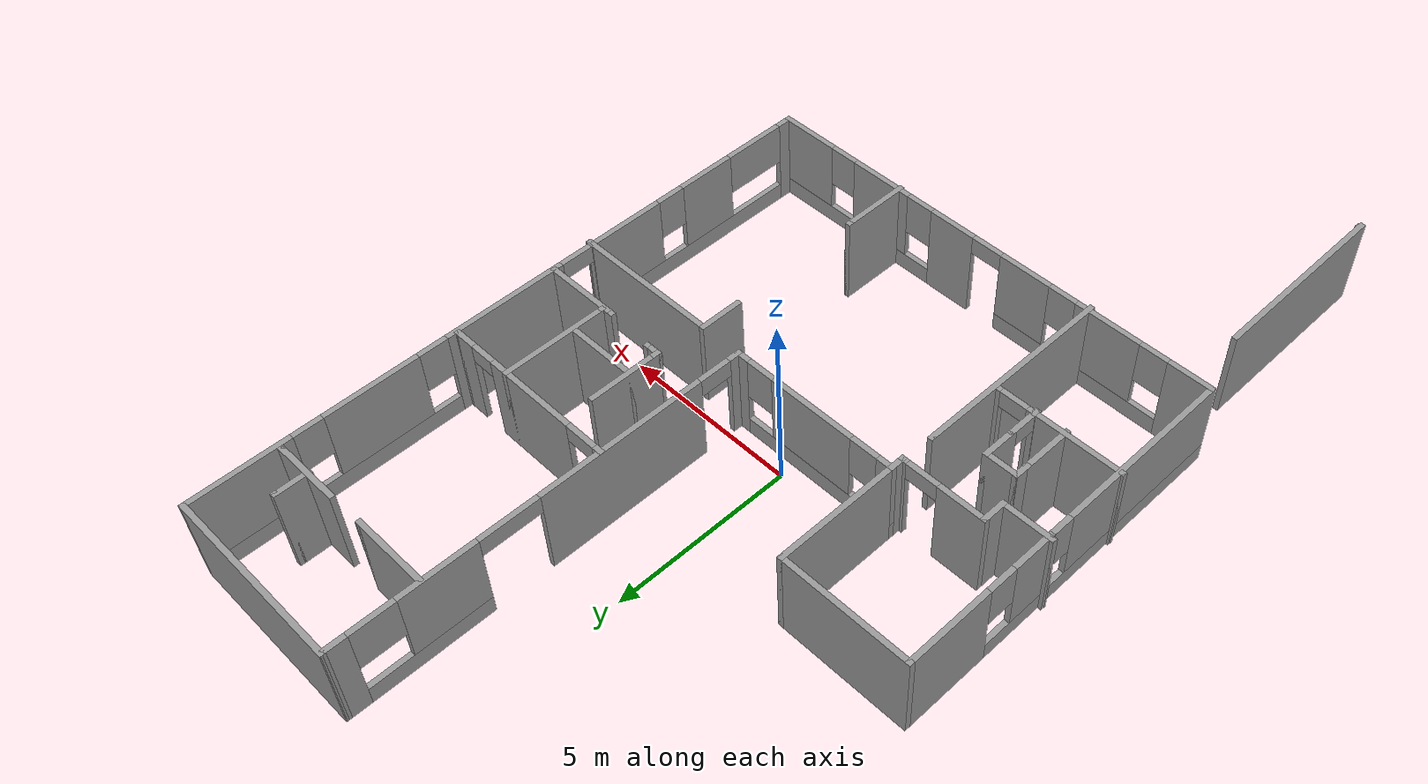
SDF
<?xml version='1.0'?>
<sdf version='1.7'>
  <model name='Floorplan6'>
    <pose>0.229791 -1.72408 0 0 -0 0</pose>
    <link name='Wall_0'>
      <collision name='Wall_0_Collision'>
        <geometry>
          <box>
            <size>3.75 0.15 2.5</size>
          </box>
        </geometry>
        <pose>0 0 1.25 0 -0 0</pose>
      </collision>
      <visual name='Wall_0_Visual'>
        <pose>0 0 1.25 0 -0 0</pose>
        <geometry>
          <box>
            <size>3.75 0.15 2.5</size>
          </box>
        </geometry>
        <material>
          <script>
            <uri>file://media/materials/scripts/gazebo.material</uri>
            <name>Gazebo/Grey</name>
          </script>
          <ambient>1 1 1 1</ambient>
        </material>
        <meta>
          <layer>0</layer>
        </meta>
      </visual>
      <pose>-4.99953 4.56763 0 0 -0 3.14159</pose>
    </link>
    <link name='Wall_1'>
      <pose>-6.79953 -0.482372 0 0 -0 -1.5708</pose>
      <visual name='Wall_1_Visual_0'>
        <pose>-3.88959 0 1.25 0 -0 0</pose>
        <geometry>
          <box>
            <size>2.47081 0.15 2.5</size>
          </box>
        </geometry>
        <material>
          <script>
            <uri>file://media/materials/scripts/gazebo.material</uri>
            <name>Gazebo/Grey</name>
          </script>
          <ambient>1 1 1 1</ambient>
        </material>
        <meta>
          <layer>0</layer>
        </meta>
      </visual>
      <collision name='Wall_1_Collision_0'>
        <geometry>
          <box>
            <size>2.47081 0.15 2.5</size>
          </box>
        </geometry>
        <pose>-3.88959 0 1.25 0 -0 0</pose>
      </collision>
      <visual name='Wall_1_Visual_1'>
        <pose>1.23541 0 0.25 0 -0 0</pose>
        <geometry>
          <box>
            <size>7.77919 0.15 0.5</size>
          </box>
        </geometry>
        <material>
          <script>
            <uri>file://media/materials/scripts/gazebo.material</uri>
            <name>Gazebo/Grey</name>
          </script>
          <ambient>1 1 1 1</ambient>
        </material>
        <meta>
          <layer>0</layer>
        </meta>
      </visual>
      <collision name='Wall_1_Collision_1'>
        <geometry>
          <box>
            <size>7.77919 0.15 0.5</size>
          </box>
        </geometry>
        <pose>1.23541 0 0.25 0 -0 0</pose>
      </collision>
      <visual name='Wall_1_Visual_2'>
        <pose>-1.23648 0 1.5 0 -0 0</pose>
        <geometry>
          <box>
            <size>1.23542 0.15 2</size>
          </box>
        </geometry>
        <material>
          <script>
            <uri>file://media/materials/scripts/gazebo.material</uri>
            <name>Gazebo/Grey</name>
          </script>
          <ambient>1 1 1 1</ambient>
        </material>
        <meta>
          <layer>0</layer>
        </meta>
      </visual>
      <collision name='Wall_1_Collision_2'>
        <geometry>
          <box>
            <size>1.23542 0.15 2</size>
          </box>
        </geometry>
        <pose>-1.23648 0 1.5 0 -0 0</pose>
      </collision>
      <visual name='Wall_1_Visual_3'>
        <pose>2.5606 0 1.5 0 -0 0</pose>
        <geometry>
          <box>
            <size>5.12881 0.15 2</size>
          </box>
        </geometry>
        <material>
          <script>
            <uri>file://media/materials/scripts/gazebo.material</uri>
            <name>Gazebo/Grey</name>
          </script>
          <ambient>1 1 1 1</ambient>
        </material>
        <meta>
          <layer>0</layer>
        </meta>
      </visual>
      <collision name='Wall_1_Collision_3'>
        <geometry>
          <box>
            <size>5.12881 0.15 2</size>
          </box>
        </geometry>
        <pose>2.5606 0 1.5 0 -0 0</pose>
      </collision>
      <visual name='Wall_1_Visual_4'>
        <pose>-2.25419 0 1.9 0 -0 0</pose>
        <geometry>
          <box>
            <size>0.8 0.15 1.2</size>
          </box>
        </geometry>
        <material>
          <script>
            <uri>file://media/materials/scripts/gazebo.material</uri>
            <name>Gazebo/Grey</name>
          </script>
          <ambient>1 1 1 1</ambient>
        </material>
        <meta>
          <layer>0</layer>
        </meta>
      </visual>
      <collision name='Wall_1_Collision_4'>
        <geometry>
          <box>
            <size>0.8 0.15 1.2</size>
          </box>
        </geometry>
        <pose>-2.25419 0 1.9 0 -0 0</pose>
      </collision>
      <visual name='Wall_1_Visual_5'>
        <pose>-0.311291 0 1.9 0 -0 0</pose>
        <geometry>
          <box>
            <size>0.614962 0.15 1.2</size>
          </box>
        </geometry>
        <material>
          <script>
            <uri>file://media/materials/scripts/gazebo.material</uri>
            <name>Gazebo/Grey</name>
          </script>
          <ambient>1 1 1 1</ambient>
        </material>
        <meta>
          <layer>0</layer>
        </meta>
      </visual>
      <collision name='Wall_1_Collision_5'>
        <geometry>
          <box>
            <size>0.614962 0.15 1.2</size>
          </box>
        </geometry>
        <pose>-0.311291 0 1.9 0 -0 0</pose>
      </collision>
    </link>
    <link name='Wall_10'>
      <collision name='Wall_10_Collision'>
        <geometry>
          <box>
            <size>0.5 0.15 2.5</size>
          </box>
        </geometry>
        <pose>0 0 1.25 0 -0 0</pose>
      </collision>
      <visual name='Wall_10_Visual'>
        <pose>0 0 1.25 0 -0 0</pose>
        <geometry>
          <box>
            <size>0.5 0.15 2.5</size>
          </box>
        </geometry>
        <material>
          <script>
            <uri>file://media/materials/scripts/gazebo.material</uri>
            <name>Gazebo/Grey</name>
          </script>
          <ambient>1 1 1 1</ambient>
        </material>
        <meta>
          <layer>0</layer>
        </meta>
      </visual>
      <pose>-3.19953 1.04263 0 0 -0 -1.5708</pose>
    </link>
    <link name='Wall_11'>
      <pose>-4.37453 0.867628 0 0 -0 3.14159</pose>
      <visual name='Wall_11_Visual_0'>
        <pose>-1.13466 0 1.25 0 -0 0</pose>
        <geometry>
          <box>
            <size>0.230674 0.15 2.5</size>
          </box>
        </geometry>
        <material>
          <script>
            <uri>file://media/materials/scripts/gazebo.material</uri>
            <name>Gazebo/Grey</name>
          </script>
          <ambient>1 1 1 1</ambient>
        </material>
        <meta>
          <layer>0</layer>
        </meta>
      </visual>
      <collision name='Wall_11_Collision_0'>
        <geometry>
          <box>
            <size>0.230674 0.15 2.5</size>
          </box>
        </geometry>
        <pose>-1.13466 0 1.25 0 -0 0</pose>
      </collision>
      <visual name='Wall_11_Visual_1'>
        <pose>0.565337 0 1.25 0 -0 0</pose>
        <geometry>
          <box>
            <size>1.36933 0.15 2.5</size>
          </box>
        </geometry>
        <material>
          <script>
            <uri>file://media/materials/scripts/gazebo.material</uri>
            <name>Gazebo/Grey</name>
          </script>
          <ambient>1 1 1 1</ambient>
        </material>
        <meta>
          <layer>0</layer>
        </meta>
      </visual>
      <collision name='Wall_11_Collision_1'>
        <geometry>
          <box>
            <size>1.36933 0.15 2.5</size>
          </box>
        </geometry>
        <pose>0.565337 0 1.25 0 -0 0</pose>
      </collision>
      <visual name='Wall_11_Visual_2'>
        <pose>-0.569326 0 2.25 0 -0 0</pose>
        <geometry>
          <box>
            <size>0.9 0.15 0.5</size>
          </box>
        </geometry>
        <material>
          <script>
            <uri>file://media/materials/scripts/gazebo.material</uri>
            <name>Gazebo/Grey</name>
          </script>
          <ambient>1 1 1 1</ambient>
        </material>
        <meta>
          <layer>0</layer>
        </meta>
      </visual>
      <collision name='Wall_11_Collision_2'>
        <geometry>
          <box>
            <size>0.9 0.15 0.5</size>
          </box>
        </geometry>
        <pose>-0.569326 0 2.25 0 -0 0</pose>
      </collision>
    </link>
    <link name='Wall_12'>
      <collision name='Wall_12_Collision'>
        <geometry>
          <box>
            <size>0.75 0.15 2.5</size>
          </box>
        </geometry>
        <pose>0 0 1.25 0 -0 0</pose>
      </collision>
      <visual name='Wall_12_Visual'>
        <pose>0 0 1.25 0 -0 0</pose>
        <geometry>
          <box>
            <size>0.75 0.15 2.5</size>
          </box>
        </geometry>
        <material>
          <script>
            <uri>file://media/materials/scripts/gazebo.material</uri>
            <name>Gazebo/Grey</name>
          </script>
          <ambient>1 1 1 1</ambient>
        </material>
        <meta>
          <layer>0</layer>
        </meta>
      </visual>
      <pose>-5.54953 0.567628 0 0 -0 -1.5708</pose>
    </link>
    <link name='Wall_13'>
      <collision name='Wall_13_Collision'>
        <geometry>
          <box>
            <size>1.5 0.15 2.5</size>
          </box>
        </geometry>
        <pose>0 0 1.25 0 -0 0</pose>
      </collision>
      <visual name='Wall_13_Visual'>
        <pose>0 0 1.25 0 -0 0</pose>
        <geometry>
          <box>
            <size>1.5 0.15 2.5</size>
          </box>
        </geometry>
        <material>
          <script>
            <uri>file://media/materials/scripts/gazebo.material</uri>
            <name>Gazebo/Grey</name>
          </script>
          <ambient>1 1 1 1</ambient>
        </material>
        <meta>
          <layer>0</layer>
        </meta>
      </visual>
      <pose>-6.22453 0.267628 0 0 -0 3.14159</pose>
    </link>
    <link name='Wall_14'>
      <collision name='Wall_14_Collision'>
        <geometry>
          <box>
            <size>0.15 0.15 2.5</size>
          </box>
        </geometry>
        <pose>0 0 1.25 0 -0 0</pose>
      </collision>
      <visual name='Wall_14_Visual'>
        <pose>0 0 1.25 0 -0 0</pose>
        <geometry>
          <box>
            <size>0.15 0.15 2.5</size>
          </box>
        </geometry>
        <material>
          <script>
            <uri>file://media/materials/scripts/gazebo.material</uri>
            <name>Gazebo/Grey</name>
          </script>
          <ambient>1 1 1 1</ambient>
        </material>
        <meta>
          <layer>0</layer>
        </meta>
      </visual>
      <pose>-6.89953 0.267628 0 0 -0 0</pose>
    </link>
    <link name='Wall_16'>
      <collision name='Wall_16_Collision'>
        <geometry>
          <box>
            <size>5.5 0.15 2.5</size>
          </box>
        </geometry>
        <pose>0 0 1.25 0 -0 0</pose>
      </collision>
      <visual name='Wall_16_Visual'>
        <pose>0 0 1.25 0 -0 0</pose>
        <geometry>
          <box>
            <size>5.5 0.15 2.5</size>
          </box>
        </geometry>
        <material>
          <script>
            <uri>file://media/materials/scripts/gazebo.material</uri>
            <name>Gazebo/Grey</name>
          </script>
          <ambient>1 1 1 1</ambient>
        </material>
        <meta>
          <layer>0</layer>
        </meta>
      </visual>
      <pose>-6.25348 -9.91858 0 0 -0 -1.5708</pose>
    </link>
    <link name='Wall_17'>
      <collision name='Wall_17_Collision'>
        <geometry>
          <box>
            <size>0.15 0.15 2.5</size>
          </box>
        </geometry>
        <pose>0 0 1.25 0 -0 0</pose>
      </collision>
      <visual name='Wall_17_Visual'>
        <pose>0 0 1.25 0 -0 0</pose>
        <geometry>
          <box>
            <size>0.15 0.15 2.5</size>
          </box>
        </geometry>
        <material>
          <script>
            <uri>file://media/materials/scripts/gazebo.material</uri>
            <name>Gazebo/Grey</name>
          </script>
          <ambient>1 1 1 1</ambient>
        </material>
        <meta>
          <layer>0</layer>
        </meta>
      </visual>
      <pose>-6.22423 -12.5351 0 0 -0 0</pose>
    </link>
    <link name='Wall_19'>
      <collision name='Wall_19_Collision'>
        <geometry>
          <box>
            <size>5.75 0.15 2.5</size>
          </box>
        </geometry>
        <pose>0 0 1.25 0 -0 0</pose>
      </collision>
      <visual name='Wall_19_Visual'>
        <pose>0 0 1.25 0 -0 0</pose>
        <geometry>
          <box>
            <size>5.75 0.15 2.5</size>
          </box>
        </geometry>
        <material>
          <script>
            <uri>file://media/materials/scripts/gazebo.material</uri>
            <name>Gazebo/Grey</name>
          </script>
          <ambient>1 1 1 1</ambient>
        </material>
        <meta>
          <layer>0</layer>
        </meta>
      </visual>
      <pose>-3.25626 -2.81943 0 0 -0 1.5708</pose>
    </link>
    <link name='Wall_2'>
      <pose>0.000472 -5.53237 0 0 -0 0</pose>
      <visual name='Wall_2_Visual_0'>
        <pose>-6.24139 0 1.25 0 -0 0</pose>
        <geometry>
          <box>
            <size>1.26723 0.15 2.5</size>
          </box>
        </geometry>
        <material>
          <script>
            <uri>file://media/materials/scripts/gazebo.material</uri>
            <name>Gazebo/Grey</name>
          </script>
          <ambient>1 1 1 1</ambient>
        </material>
        <meta>
          <layer>0</layer>
        </meta>
      </visual>
      <collision name='Wall_2_Collision_0'>
        <geometry>
          <box>
            <size>1.26723 0.15 2.5</size>
          </box>
        </geometry>
        <pose>-6.24139 0 1.25 0 -0 0</pose>
      </collision>
      <visual name='Wall_2_Visual_1'>
        <pose>0.98447 0 1.25 0 -0 0</pose>
        <geometry>
          <box>
            <size>1.36771 0.15 2.5</size>
          </box>
        </geometry>
        <material>
          <script>
            <uri>file://media/materials/scripts/gazebo.material</uri>
            <name>Gazebo/Grey</name>
          </script>
          <ambient>1 1 1 1</ambient>
        </material>
        <meta>
          <layer>0</layer>
        </meta>
      </visual>
      <collision name='Wall_2_Collision_1'>
        <geometry>
          <box>
            <size>1.36771 0.15 2.5</size>
          </box>
        </geometry>
        <pose>0.98447 0 1.25 0 -0 0</pose>
      </collision>
      <visual name='Wall_2_Visual_2'>
        <pose>-3.10358 0 0.25 0 -0 0</pose>
        <geometry>
          <box>
            <size>5.00839 0.15 0.5</size>
          </box>
        </geometry>
        <material>
          <script>
            <uri>file://media/materials/scripts/gazebo.material</uri>
            <name>Gazebo/Grey</name>
          </script>
          <ambient>1 1 1 1</ambient>
        </material>
        <meta>
          <layer>0</layer>
        </meta>
      </visual>
      <collision name='Wall_2_Collision_2'>
        <geometry>
          <box>
            <size>5.00839 0.15 0.5</size>
          </box>
        </geometry>
        <pose>-3.10358 0 0.25 0 -0 0</pose>
      </collision>
      <visual name='Wall_2_Visual_3'>
        <pose>4.27166 0 0.25 0 -0 0</pose>
        <geometry>
          <box>
            <size>5.20668 0.15 0.5</size>
          </box>
        </geometry>
        <material>
          <script>
            <uri>file://media/materials/scripts/gazebo.material</uri>
            <name>Gazebo/Grey</name>
          </script>
          <ambient>1 1 1 1</ambient>
        </material>
        <meta>
          <layer>0</layer>
        </meta>
      </visual>
      <collision name='Wall_2_Collision_3'>
        <geometry>
          <box>
            <size>5.20668 0.15 0.5</size>
          </box>
        </geometry>
        <pose>4.27166 0 0.25 0 -0 0</pose>
      </collision>
      <visual name='Wall_2_Visual_4'>
        <pose>-3.86128 0 1.5 0 -0 0</pose>
        <geometry>
          <box>
            <size>1.89299 0.15 2</size>
          </box>
        </geometry>
        <material>
          <script>
            <uri>file://media/materials/scripts/gazebo.material</uri>
            <name>Gazebo/Grey</name>
          </script>
          <ambient>1 1 1 1</ambient>
        </material>
        <meta>
          <layer>0</layer>
        </meta>
      </visual>
      <collision name='Wall_2_Collision_4'>
        <geometry>
          <box>
            <size>1.89299 0.15 2</size>
          </box>
        </geometry>
        <pose>-3.86128 0 1.5 0 -0 0</pose>
      </collision>
      <visual name='Wall_2_Visual_5'>
        <pose>-1.35708 0 1.5 0 -0 0</pose>
        <geometry>
          <box>
            <size>1.5154 0.15 2</size>
          </box>
        </geometry>
        <material>
          <script>
            <uri>file://media/materials/scripts/gazebo.material</uri>
            <name>Gazebo/Grey</name>
          </script>
          <ambient>1 1 1 1</ambient>
        </material>
        <meta>
          <layer>0</layer>
        </meta>
      </visual>
      <collision name='Wall_2_Collision_5'>
        <geometry>
          <box>
            <size>1.5154 0.15 2</size>
          </box>
        </geometry>
        <pose>-1.35708 0 1.5 0 -0 0</pose>
      </collision>
      <visual name='Wall_2_Visual_6'>
        <pose>-1.35708 0 1.5 0 -0 0</pose>
        <geometry>
          <box>
            <size>1.5154 0.15 2</size>
          </box>
        </geometry>
        <material>
          <script>
            <uri>file://media/materials/scripts/gazebo.material</uri>
            <name>Gazebo/Grey</name>
          </script>
          <ambient>1 1 1 1</ambient>
        </material>
        <meta>
          <layer>0</layer>
        </meta>
      </visual>
      <collision name='Wall_2_Collision_6'>
        <geometry>
          <box>
            <size>1.5154 0.15 2</size>
          </box>
        </geometry>
        <pose>-1.35708 0 1.5 0 -0 0</pose>
      </collision>
      <visual name='Wall_2_Visual_7'>
        <pose>3.39809 0 1.5 0 -0 0</pose>
        <geometry>
          <box>
            <size>1.85954 0.15 2</size>
          </box>
        </geometry>
        <material>
          <script>
            <uri>file://media/materials/scripts/gazebo.material</uri>
            <name>Gazebo/Grey</name>
          </script>
          <ambient>1 1 1 1</ambient>
        </material>
        <meta>
          <layer>0</layer>
        </meta>
      </visual>
      <collision name='Wall_2_Collision_7'>
        <geometry>
          <box>
            <size>1.85954 0.15 2</size>
          </box>
        </geometry>
        <pose>3.39809 0 1.5 0 -0 0</pose>
      </collision>
      <visual name='Wall_2_Visual_8'>
        <pose>6.00143 0 1.5 0 -0 0</pose>
        <geometry>
          <box>
            <size>1.74714 0.15 2</size>
          </box>
        </geometry>
        <material>
          <script>
            <uri>file://media/materials/scripts/gazebo.material</uri>
            <name>Gazebo/Grey</name>
          </script>
          <ambient>1 1 1 1</ambient>
        </material>
        <meta>
          <layer>0</layer>
        </meta>
      </visual>
      <collision name='Wall_2_Collision_8'>
        <geometry>
          <box>
            <size>1.74714 0.15 2</size>
          </box>
        </geometry>
        <pose>6.00143 0 1.5 0 -0 0</pose>
      </collision>
      <visual name='Wall_2_Visual_9'>
        <pose>-5.20777 0 1.9 0 -0 0</pose>
        <geometry>
          <box>
            <size>0.8 0.15 1.2</size>
          </box>
        </geometry>
        <material>
          <script>
            <uri>file://media/materials/scripts/gazebo.material</uri>
            <name>Gazebo/Grey</name>
          </script>
          <ambient>1 1 1 1</ambient>
        </material>
        <meta>
          <layer>0</layer>
        </meta>
      </visual>
      <collision name='Wall_2_Collision_9'>
        <geometry>
          <box>
            <size>0.8 0.15 1.2</size>
          </box>
        </geometry>
        <pose>-5.20777 0 1.9 0 -0 0</pose>
      </collision>
      <visual name='Wall_2_Visual_10'>
        <pose>2.06832 0 1.9 0 -0 0</pose>
        <geometry>
          <box>
            <size>0.8 0.15 1.2</size>
          </box>
        </geometry>
        <material>
          <script>
            <uri>file://media/materials/scripts/gazebo.material</uri>
            <name>Gazebo/Grey</name>
          </script>
          <ambient>1 1 1 1</ambient>
        </material>
        <meta>
          <layer>0</layer>
        </meta>
      </visual>
      <collision name='Wall_2_Collision_10'>
        <geometry>
          <box>
            <size>0.8 0.15 1.2</size>
          </box>
        </geometry>
        <pose>2.06832 0 1.9 0 -0 0</pose>
      </collision>
      <visual name='Wall_2_Visual_11'>
        <pose>-2.51478 0 1.9 0 -0 0</pose>
        <geometry>
          <box>
            <size>0.8 0.15 1.2</size>
          </box>
        </geometry>
        <material>
          <script>
            <uri>file://media/materials/scripts/gazebo.material</uri>
            <name>Gazebo/Grey</name>
          </script>
          <ambient>1 1 1 1</ambient>
        </material>
        <meta>
          <layer>0</layer>
        </meta>
      </visual>
      <collision name='Wall_2_Collision_11'>
        <geometry>
          <box>
            <size>0.8 0.15 1.2</size>
          </box>
        </geometry>
        <pose>-2.51478 0 1.9 0 -0 0</pose>
      </collision>
      <visual name='Wall_2_Visual_12'>
        <pose>4.72786 0 1.9 0 -0 0</pose>
        <geometry>
          <box>
            <size>0.8 0.15 1.2</size>
          </box>
        </geometry>
        <material>
          <script>
            <uri>file://media/materials/scripts/gazebo.material</uri>
            <name>Gazebo/Grey</name>
          </script>
          <ambient>1 1 1 1</ambient>
        </material>
        <meta>
          <layer>0</layer>
        </meta>
      </visual>
      <collision name='Wall_2_Collision_12'>
        <geometry>
          <box>
            <size>0.8 0.15 1.2</size>
          </box>
        </geometry>
        <pose>4.72786 0 1.9 0 -0 0</pose>
      </collision>
      <visual name='Wall_2_Visual_13'>
        <pose>-0.149383 0 2.25 0 -0 0</pose>
        <geometry>
          <box>
            <size>0.9 0.15 0.5</size>
          </box>
        </geometry>
        <material>
          <script>
            <uri>file://media/materials/scripts/gazebo.material</uri>
            <name>Gazebo/Grey</name>
          </script>
          <ambient>1 1 1 1</ambient>
        </material>
        <meta>
          <layer>0</layer>
        </meta>
      </visual>
      <collision name='Wall_2_Collision_13'>
        <geometry>
          <box>
            <size>0.9 0.15 0.5</size>
          </box>
        </geometry>
        <pose>-0.149383 0 2.25 0 -0 0</pose>
      </collision>
      <visual name='Wall_2_Visual_14'>
        <pose>-0.149383 0 2.25 0 -0 0</pose>
        <geometry>
          <box>
            <size>0.9 0.15 0.5</size>
          </box>
        </geometry>
        <material>
          <script>
            <uri>file://media/materials/scripts/gazebo.material</uri>
            <name>Gazebo/Grey</name>
          </script>
          <ambient>1 1 1 1</ambient>
        </material>
        <meta>
          <layer>0</layer>
        </meta>
      </visual>
      <collision name='Wall_2_Collision_14'>
        <geometry>
          <box>
            <size>0.9 0.15 0.5</size>
          </box>
        </geometry>
        <pose>-0.149383 0 2.25 0 -0 0</pose>
      </collision>
    </link>
    <link name='Wall_20'>
      <collision name='Wall_20_Collision'>
        <geometry>
          <box>
            <size>0.15 0.15 2.5</size>
          </box>
        </geometry>
        <pose>0 0 1.25 0 -0 0</pose>
      </collision>
      <visual name='Wall_20_Visual'>
        <pose>0 0 1.25 0 -0 0</pose>
        <geometry>
          <box>
            <size>0.15 0.15 2.5</size>
          </box>
        </geometry>
        <material>
          <script>
            <uri>file://media/materials/scripts/gazebo.material</uri>
            <name>Gazebo/Grey</name>
          </script>
          <ambient>1 1 1 1</ambient>
        </material>
        <meta>
          <layer>0</layer>
        </meta>
      </visual>
      <pose>-3.25626 -0.019432 0 0 -0 0</pose>
    </link>
    <link name='Wall_22'>
      <pose>-5.05626 -2.16734 0 0 -0 3.14159</pose>
      <visual name='Wall_22_Visual_0'>
        <pose>-1.74129 0 1.25 0 -0 0</pose>
        <geometry>
          <box>
            <size>0.267415 0.15 2.5</size>
          </box>
        </geometry>
        <material>
          <script>
            <uri>file://media/materials/scripts/gazebo.material</uri>
            <name>Gazebo/Grey</name>
          </script>
          <ambient>1 1 1 1</ambient>
        </material>
        <meta>
          <layer>0</layer>
        </meta>
      </visual>
      <collision name='Wall_22_Collision_0'>
        <geometry>
          <box>
            <size>0.267415 0.15 2.5</size>
          </box>
        </geometry>
        <pose>-1.74129 0 1.25 0 -0 0</pose>
      </collision>
      <visual name='Wall_22_Visual_1'>
        <pose>0.516421 0 1.25 0 -0 0</pose>
        <geometry>
          <box>
            <size>2.71716 0.15 2.5</size>
          </box>
        </geometry>
        <material>
          <script>
            <uri>file://media/materials/scripts/gazebo.material</uri>
            <name>Gazebo/Grey</name>
          </script>
          <ambient>1 1 1 1</ambient>
        </material>
        <meta>
          <layer>0</layer>
        </meta>
      </visual>
      <collision name='Wall_22_Collision_1'>
        <geometry>
          <box>
            <size>2.71716 0.15 2.5</size>
          </box>
        </geometry>
        <pose>0.516421 0 1.25 0 -0 0</pose>
      </collision>
      <visual name='Wall_22_Visual_2'>
        <pose>-1.22487 0 2.25 0 -0 0</pose>
        <geometry>
          <box>
            <size>0.765427 0.15 0.5</size>
          </box>
        </geometry>
        <material>
          <script>
            <uri>file://media/materials/scripts/gazebo.material</uri>
            <name>Gazebo/Grey</name>
          </script>
          <ambient>1 1 1 1</ambient>
        </material>
        <meta>
          <layer>0</layer>
        </meta>
      </visual>
      <collision name='Wall_22_Collision_2'>
        <geometry>
          <box>
            <size>0.765427 0.15 0.5</size>
          </box>
        </geometry>
        <pose>-1.22487 0 2.25 0 -0 0</pose>
      </collision>
    </link>
    <link name='Wall_23'>
      <collision name='Wall_23_Collision'>
        <geometry>
          <box>
            <size>0.15 0.15 2.5</size>
          </box>
        </geometry>
        <pose>0 0 1.25 0 -0 0</pose>
      </collision>
      <visual name='Wall_23_Visual'>
        <pose>0 0 1.25 0 -0 0</pose>
        <geometry>
          <box>
            <size>0.15 0.15 2.5</size>
          </box>
        </geometry>
        <material>
          <script>
            <uri>file://media/materials/scripts/gazebo.material</uri>
            <name>Gazebo/Grey</name>
          </script>
          <ambient>1 1 1 1</ambient>
        </material>
        <meta>
          <layer>0</layer>
        </meta>
      </visual>
      <pose>-6.85626 -2.16734 0 0 -0 0</pose>
    </link>
    <link name='Wall_25'>
      <collision name='Wall_25_Collision'>
        <geometry>
          <box>
            <size>1.5 0.15 2.5</size>
          </box>
        </geometry>
        <pose>0 0 1.25 0 -0 0</pose>
      </collision>
      <visual name='Wall_25_Visual'>
        <pose>0 0 1.25 0 -0 0</pose>
        <geometry>
          <box>
            <size>1.5 0.15 2.5</size>
          </box>
        </geometry>
        <material>
          <script>
            <uri>file://media/materials/scripts/gazebo.material</uri>
            <name>Gazebo/Grey</name>
          </script>
          <ambient>1 1 1 1</ambient>
        </material>
        <meta>
          <layer>0</layer>
        </meta>
      </visual>
      <pose>-5.26023 -1.55085 0 0 -0 1.5708</pose>
    </link>
    <link name='Wall_26'>
      <collision name='Wall_26_Collision'>
        <geometry>
          <box>
            <size>0.5 0.15 2.5</size>
          </box>
        </geometry>
        <pose>0 0 1.25 0 -0 0</pose>
      </collision>
      <visual name='Wall_26_Visual'>
        <pose>0 0 1.25 0 -0 0</pose>
        <geometry>
          <box>
            <size>0.5 0.15 2.5</size>
          </box>
        </geometry>
        <material>
          <script>
            <uri>file://media/materials/scripts/gazebo.material</uri>
            <name>Gazebo/Grey</name>
          </script>
          <ambient>1 1 1 1</ambient>
        </material>
        <meta>
          <layer>0</layer>
        </meta>
      </visual>
      <pose>-5.26023 -0.700848 0 0 -0 1.5708</pose>
    </link>
    <link name='Wall_27'>
      <collision name='Wall_27_Collision'>
        <geometry>
          <box>
            <size>1 0.15 2.5</size>
          </box>
        </geometry>
        <pose>0 0 1.25 0 -0 0</pose>
      </collision>
      <visual name='Wall_27_Visual'>
        <pose>0 0 1.25 0 -0 0</pose>
        <geometry>
          <box>
            <size>1 0.15 2.5</size>
          </box>
        </geometry>
        <material>
          <script>
            <uri>file://media/materials/scripts/gazebo.material</uri>
            <name>Gazebo/Grey</name>
          </script>
          <ambient>1 1 1 1</ambient>
        </material>
        <meta>
          <layer>0</layer>
        </meta>
      </visual>
      <pose>-4.83523 -0.525848 0 0 -0 0</pose>
    </link>
    <link name='Wall_28'>
      <collision name='Wall_28_Collision'>
        <geometry>
          <box>
            <size>1 0.15 2.5</size>
          </box>
        </geometry>
        <pose>0 0 1.25 0 -0 0</pose>
      </collision>
      <visual name='Wall_28_Visual'>
        <pose>0 0 1.25 0 -0 0</pose>
        <geometry>
          <box>
            <size>1 0.15 2.5</size>
          </box>
        </geometry>
        <material>
          <script>
            <uri>file://media/materials/scripts/gazebo.material</uri>
            <name>Gazebo/Grey</name>
          </script>
          <ambient>1 1 1 1</ambient>
        </material>
        <meta>
          <layer>0</layer>
        </meta>
      </visual>
      <pose>-4.41023 -0.950848 0 0 -0 -1.5708</pose>
    </link>
    <link name='Wall_29'>
      <pose>-4.41023 -1.80085 0 0 -0 -1.5708</pose>
      <visual name='Wall_29_Visual_0'>
        <pose>-0.466347 0 1.25 0 -0 0</pose>
        <geometry>
          <box>
            <size>0.067305 0.15 2.5</size>
          </box>
        </geometry>
        <material>
          <script>
            <uri>file://media/materials/scripts/gazebo.material</uri>
            <name>Gazebo/Grey</name>
          </script>
          <ambient>1 1 1 1</ambient>
        </material>
        <meta>
          <layer>0</layer>
        </meta>
      </visual>
      <collision name='Wall_29_Collision_0'>
        <geometry>
          <box>
            <size>0.067305 0.15 2.5</size>
          </box>
        </geometry>
        <pose>-0.466347 0 1.25 0 -0 0</pose>
      </collision>
      <visual name='Wall_29_Visual_1'>
        <pose>0.385475 0 1.25 0 -0 0</pose>
        <geometry>
          <box>
            <size>0.229051 0.15 2.5</size>
          </box>
        </geometry>
        <material>
          <script>
            <uri>file://media/materials/scripts/gazebo.material</uri>
            <name>Gazebo/Grey</name>
          </script>
          <ambient>1 1 1 1</ambient>
        </material>
        <meta>
          <layer>0</layer>
        </meta>
      </visual>
      <collision name='Wall_29_Collision_1'>
        <geometry>
          <box>
            <size>0.229051 0.15 2.5</size>
          </box>
        </geometry>
        <pose>0.385475 0 1.25 0 -0 0</pose>
      </collision>
      <visual name='Wall_29_Visual_2'>
        <pose>-0.080873 0 2.25 0 -0 0</pose>
        <geometry>
          <box>
            <size>0.703644 0.15 0.5</size>
          </box>
        </geometry>
        <material>
          <script>
            <uri>file://media/materials/scripts/gazebo.material</uri>
            <name>Gazebo/Grey</name>
          </script>
          <ambient>1 1 1 1</ambient>
        </material>
        <meta>
          <layer>0</layer>
        </meta>
      </visual>
      <collision name='Wall_29_Collision_2'>
        <geometry>
          <box>
            <size>0.703644 0.15 0.5</size>
          </box>
        </geometry>
        <pose>-0.080873 0 2.25 0 -0 0</pose>
      </collision>
    </link>
    <link name='Wall_3'>
      <pose>6.80047 3.51763 0 0 -0 1.5708</pose>
      <visual name='Wall_3_Visual_0'>
        <pose>-8.87733 0 1.25 0 -0 0</pose>
        <geometry>
          <box>
            <size>0.495347 0.15 2.5</size>
          </box>
        </geometry>
        <material>
          <script>
            <uri>file://media/materials/scripts/gazebo.material</uri>
            <name>Gazebo/Grey</name>
          </script>
          <ambient>1 1 1 1</ambient>
        </material>
        <meta>
          <layer>0</layer>
        </meta>
      </visual>
      <collision name='Wall_3_Collision_0'>
        <geometry>
          <box>
            <size>0.495347 0.15 2.5</size>
          </box>
        </geometry>
        <pose>-8.87733 0 1.25 0 -0 0</pose>
      </collision>
      <visual name='Wall_3_Visual_1'>
        <pose>0.426989 0 1.25 0 -0 0</pose>
        <geometry>
          <box>
            <size>3.4456 0.15 2.5</size>
          </box>
        </geometry>
        <material>
          <script>
            <uri>file://media/materials/scripts/gazebo.material</uri>
            <name>Gazebo/Grey</name>
          </script>
          <ambient>1 1 1 1</ambient>
        </material>
        <meta>
          <layer>0</layer>
        </meta>
      </visual>
      <collision name='Wall_3_Collision_1'>
        <geometry>
          <box>
            <size>3.4456 0.15 2.5</size>
          </box>
        </geometry>
        <pose>0.426989 0 1.25 0 -0 0</pose>
      </collision>
      <visual name='Wall_3_Visual_2'>
        <pose>-5.41273 0 0.25 0 -0 0</pose>
        <geometry>
          <box>
            <size>6.43384 0.15 0.5</size>
          </box>
        </geometry>
        <material>
          <script>
            <uri>file://media/materials/scripts/gazebo.material</uri>
            <name>Gazebo/Grey</name>
          </script>
          <ambient>1 1 1 1</ambient>
        </material>
        <meta>
          <layer>0</layer>
        </meta>
      </visual>
      <collision name='Wall_3_Collision_2'>
        <geometry>
          <box>
            <size>6.43384 0.15 0.5</size>
          </box>
        </geometry>
        <pose>-5.41273 0 0.25 0 -0 0</pose>
      </collision>
      <visual name='Wall_3_Visual_3'>
        <pose>5.63739 0 0.25 0 -0 0</pose>
        <geometry>
          <box>
            <size>6.97521 0.15 0.5</size>
          </box>
        </geometry>
        <material>
          <script>
            <uri>file://media/materials/scripts/gazebo.material</uri>
            <name>Gazebo/Grey</name>
          </script>
          <ambient>1 1 1 1</ambient>
        </material>
        <meta>
          <layer>0</layer>
        </meta>
      </visual>
      <collision name='Wall_3_Collision_3'>
        <geometry>
          <box>
            <size>6.97521 0.15 0.5</size>
          </box>
        </geometry>
        <pose>5.63739 0 0.25 0 -0 0</pose>
      </collision>
      <visual name='Wall_3_Visual_4'>
        <pose>-6.03846 0 1.5 0 -0 0</pose>
        <geometry>
          <box>
            <size>1.64209 0.15 2</size>
          </box>
        </geometry>
        <material>
          <script>
            <uri>file://media/materials/scripts/gazebo.material</uri>
            <name>Gazebo/Grey</name>
          </script>
          <ambient>1 1 1 1</ambient>
        </material>
        <meta>
          <layer>0</layer>
        </meta>
      </visual>
      <collision name='Wall_3_Collision_4'>
        <geometry>
          <box>
            <size>1.64209 0.15 2</size>
          </box>
        </geometry>
        <pose>-6.03846 0 1.5 0 -0 0</pose>
      </collision>
      <visual name='Wall_3_Visual_5'>
        <pose>-3.30661 0 1.5 0 -0 0</pose>
        <geometry>
          <box>
            <size>2.2216 0.15 2</size>
          </box>
        </geometry>
        <material>
          <script>
            <uri>file://media/materials/scripts/gazebo.material</uri>
            <name>Gazebo/Grey</name>
          </script>
          <ambient>1 1 1 1</ambient>
        </material>
        <meta>
          <layer>0</layer>
        </meta>
      </visual>
      <collision name='Wall_3_Collision_5'>
        <geometry>
          <box>
            <size>2.2216 0.15 2</size>
          </box>
        </geometry>
        <pose>-3.30661 0 1.5 0 -0 0</pose>
      </collision>
      <visual name='Wall_3_Visual_6'>
        <pose>-3.30661 0 1.5 0 -0 0</pose>
        <geometry>
          <box>
            <size>2.2216 0.15 2</size>
          </box>
        </geometry>
        <material>
          <script>
            <uri>file://media/materials/scripts/gazebo.material</uri>
            <name>Gazebo/Grey</name>
          </script>
          <ambient>1 1 1 1</ambient>
        </material>
        <meta>
          <layer>0</layer>
        </meta>
      </visual>
      <collision name='Wall_3_Collision_6'>
        <geometry>
          <box>
            <size>2.2216 0.15 2</size>
          </box>
        </geometry>
        <pose>-3.30661 0 1.5 0 -0 0</pose>
      </collision>
      <visual name='Wall_3_Visual_7'>
        <pose>4.25214 0 1.5 0 -0 0</pose>
        <geometry>
          <box>
            <size>2.6047 0.15 2</size>
          </box>
        </geometry>
        <material>
          <script>
            <uri>file://media/materials/scripts/gazebo.material</uri>
            <name>Gazebo/Grey</name>
          </script>
          <ambient>1 1 1 1</ambient>
        </material>
        <meta>
          <layer>0</layer>
        </meta>
      </visual>
      <collision name='Wall_3_Collision_7'>
        <geometry>
          <box>
            <size>2.6047 0.15 2</size>
          </box>
        </geometry>
        <pose>4.25214 0 1.5 0 -0 0</pose>
      </collision>
      <visual name='Wall_3_Visual_8'>
        <pose>7.73974 0 1.5 0 -0 0</pose>
        <geometry>
          <box>
            <size>2.77051 0.15 2</size>
          </box>
        </geometry>
        <material>
          <script>
            <uri>file://media/materials/scripts/gazebo.material</uri>
            <name>Gazebo/Grey</name>
          </script>
          <ambient>1 1 1 1</ambient>
        </material>
        <meta>
          <layer>0</layer>
        </meta>
      </visual>
      <collision name='Wall_3_Collision_8'>
        <geometry>
          <box>
            <size>2.77051 0.15 2</size>
          </box>
        </geometry>
        <pose>7.73974 0 1.5 0 -0 0</pose>
      </collision>
      <visual name='Wall_3_Visual_9'>
        <pose>-7.74458 0 1.9 0 -0 0</pose>
        <geometry>
          <box>
            <size>1.77015 0.15 1.2</size>
          </box>
        </geometry>
        <material>
          <script>
            <uri>file://media/materials/scripts/gazebo.material</uri>
            <name>Gazebo/Grey</name>
          </script>
          <ambient>1 1 1 1</ambient>
        </material>
        <meta>
          <layer>0</layer>
        </meta>
      </visual>
      <collision name='Wall_3_Collision_9'>
        <geometry>
          <box>
            <size>1.77015 0.15 1.2</size>
          </box>
        </geometry>
        <pose>-7.74458 0 1.9 0 -0 0</pose>
      </collision>
      <visual name='Wall_3_Visual_10'>
        <pose>2.54979 0 1.9 0 -0 0</pose>
        <geometry>
          <box>
            <size>0.8 0.15 1.2</size>
          </box>
        </geometry>
        <material>
          <script>
            <uri>file://media/materials/scripts/gazebo.material</uri>
            <name>Gazebo/Grey</name>
          </script>
          <ambient>1 1 1 1</ambient>
        </material>
        <meta>
          <layer>0</layer>
        </meta>
      </visual>
      <collision name='Wall_3_Collision_10'>
        <geometry>
          <box>
            <size>0.8 0.15 1.2</size>
          </box>
        </geometry>
        <pose>2.54979 0 1.9 0 -0 0</pose>
      </collision>
      <visual name='Wall_3_Visual_11'>
        <pose>-4.81741 0 1.9 0 -0 0</pose>
        <geometry>
          <box>
            <size>0.8 0.15 1.2</size>
          </box>
        </geometry>
        <material>
          <script>
            <uri>file://media/materials/scripts/gazebo.material</uri>
            <name>Gazebo/Grey</name>
          </script>
          <ambient>1 1 1 1</ambient>
        </material>
        <meta>
          <layer>0</layer>
        </meta>
      </visual>
      <collision name='Wall_3_Collision_11'>
        <geometry>
          <box>
            <size>0.8 0.15 1.2</size>
          </box>
        </geometry>
        <pose>-4.81741 0 1.9 0 -0 0</pose>
      </collision>
      <visual name='Wall_3_Visual_12'>
        <pose>5.95449 0 1.9 0 -0 0</pose>
        <geometry>
          <box>
            <size>0.8 0.15 1.2</size>
          </box>
        </geometry>
        <material>
          <script>
            <uri>file://media/materials/scripts/gazebo.material</uri>
            <name>Gazebo/Grey</name>
          </script>
          <ambient>1 1 1 1</ambient>
        </material>
        <meta>
          <layer>0</layer>
        </meta>
      </visual>
      <collision name='Wall_3_Collision_12'>
        <geometry>
          <box>
            <size>0.8 0.15 1.2</size>
          </box>
        </geometry>
        <pose>5.95449 0 1.9 0 -0 0</pose>
      </collision>
      <visual name='Wall_3_Visual_13'>
        <pose>-1.74581 0 2.25 0 -0 0</pose>
        <geometry>
          <box>
            <size>0.9 0.15 0.5</size>
          </box>
        </geometry>
        <material>
          <script>
            <uri>file://media/materials/scripts/gazebo.material</uri>
            <name>Gazebo/Grey</name>
          </script>
          <ambient>1 1 1 1</ambient>
        </material>
        <meta>
          <layer>0</layer>
        </meta>
      </visual>
      <collision name='Wall_3_Collision_13'>
        <geometry>
          <box>
            <size>0.9 0.15 0.5</size>
          </box>
        </geometry>
        <pose>-1.74581 0 2.25 0 -0 0</pose>
      </collision>
      <visual name='Wall_3_Visual_14'>
        <pose>-1.74581 0 2.25 0 -0 0</pose>
        <geometry>
          <box>
            <size>0.9 0.15 0.5</size>
          </box>
        </geometry>
        <material>
          <script>
            <uri>file://media/materials/scripts/gazebo.material</uri>
            <name>Gazebo/Grey</name>
          </script>
          <ambient>1 1 1 1</ambient>
        </material>
        <meta>
          <layer>0</layer>
        </meta>
      </visual>
      <collision name='Wall_3_Collision_14'>
        <geometry>
          <box>
            <size>0.9 0.15 0.5</size>
          </box>
        </geometry>
        <pose>-1.74581 0 2.25 0 -0 0</pose>
      </collision>
    </link>
    <link name='Wall_30'>
      <collision name='Wall_30_Collision'>
        <geometry>
          <box>
            <size>0.15 0.15 2.5</size>
          </box>
        </geometry>
        <pose>0 0 1.25 0 -0 0</pose>
      </collision>
      <visual name='Wall_30_Visual'>
        <pose>0 0 1.25 0 -0 0</pose>
        <geometry>
          <box>
            <size>0.15 0.15 2.5</size>
          </box>
        </geometry>
        <material>
          <script>
            <uri>file://media/materials/scripts/gazebo.material</uri>
            <name>Gazebo/Grey</name>
          </script>
          <ambient>1 1 1 1</ambient>
        </material>
        <meta>
          <layer>0</layer>
        </meta>
      </visual>
      <pose>-4.41023 -2.22585 0 0 -0 0</pose>
    </link>
    <link name='Wall_32'>
      <collision name='Wall_32_Collision'>
        <geometry>
          <box>
            <size>2 0.15 2.5</size>
          </box>
        </geometry>
        <pose>0 0 1.25 0 -0 0</pose>
      </collision>
      <visual name='Wall_32_Visual'>
        <pose>0 0 1.25 0 -0 0</pose>
        <geometry>
          <box>
            <size>2 0.15 2.5</size>
          </box>
        </geometry>
        <material>
          <script>
            <uri>file://media/materials/scripts/gazebo.material</uri>
            <name>Gazebo/Grey</name>
          </script>
          <ambient>1 1 1 1</ambient>
        </material>
        <meta>
          <layer>0</layer>
        </meta>
      </visual>
      <pose>2.82878 -4.65055 0 0 -0 1.5708</pose>
    </link>
    <link name='Wall_33'>
      <collision name='Wall_33_Collision'>
        <geometry>
          <box>
            <size>0.15 0.15 2.5</size>
          </box>
        </geometry>
        <pose>0 0 1.25 0 -0 0</pose>
      </collision>
      <visual name='Wall_33_Visual'>
        <pose>0 0 1.25 0 -0 0</pose>
        <geometry>
          <box>
            <size>0.15 0.15 2.5</size>
          </box>
        </geometry>
        <material>
          <script>
            <uri>file://media/materials/scripts/gazebo.material</uri>
            <name>Gazebo/Grey</name>
          </script>
          <ambient>1 1 1 1</ambient>
        </material>
        <meta>
          <layer>0</layer>
        </meta>
      </visual>
      <pose>2.82878 -3.72555 0 0 -0 0</pose>
    </link>
    <link name='Wall_35'>
      <collision name='Wall_35_Collision'>
        <geometry>
          <box>
            <size>1.25 0.15 2.5</size>
          </box>
        </geometry>
        <pose>0 0 1.25 0 -0 0</pose>
      </collision>
      <visual name='Wall_35_Visual'>
        <pose>0 0 1.25 0 -0 0</pose>
        <geometry>
          <box>
            <size>1.25 0.15 2.5</size>
          </box>
        </geometry>
        <material>
          <script>
            <uri>file://media/materials/scripts/gazebo.material</uri>
            <name>Gazebo/Grey</name>
          </script>
          <ambient>1 1 1 1</ambient>
        </material>
        <meta>
          <layer>0</layer>
        </meta>
      </visual>
      <pose>2.79953 0.679182 0 0 -0 1.5708</pose>
    </link>
    <link name='Wall_36'>
      <collision name='Wall_36_Collision'>
        <geometry>
          <box>
            <size>4.25 0.15 2.5</size>
          </box>
        </geometry>
        <pose>0 0 1.25 0 -0 0</pose>
      </collision>
      <visual name='Wall_36_Visual'>
        <pose>0 0 1.25 0 -0 0</pose>
        <geometry>
          <box>
            <size>4.25 0.15 2.5</size>
          </box>
        </geometry>
        <material>
          <script>
            <uri>file://media/materials/scripts/gazebo.material</uri>
            <name>Gazebo/Grey</name>
          </script>
          <ambient>1 1 1 1</ambient>
        </material>
        <meta>
          <layer>0</layer>
        </meta>
      </visual>
      <pose>4.84953 1.22918 0 0 -0 0</pose>
    </link>
    <link name='Wall_37'>
      <collision name='Wall_37_Collision'>
        <geometry>
          <box>
            <size>0.15 0.15 2.5</size>
          </box>
        </geometry>
        <pose>0 0 1.25 0 -0 0</pose>
      </collision>
      <visual name='Wall_37_Visual'>
        <pose>0 0 1.25 0 -0 0</pose>
        <geometry>
          <box>
            <size>0.15 0.15 2.5</size>
          </box>
        </geometry>
        <material>
          <script>
            <uri>file://media/materials/scripts/gazebo.material</uri>
            <name>Gazebo/Grey</name>
          </script>
          <ambient>1 1 1 1</ambient>
        </material>
        <meta>
          <layer>0</layer>
        </meta>
      </visual>
      <pose>6.89953 1.22918 0 0 -0 0</pose>
    </link>
    <link name='Wall_39'>
      <collision name='Wall_39_Collision'>
        <geometry>
          <box>
            <size>2.25 0.15 2.5</size>
          </box>
        </geometry>
        <pose>0 0 1.25 0 -0 0</pose>
      </collision>
      <visual name='Wall_39_Visual'>
        <pose>0 0 1.25 0 -0 0</pose>
        <geometry>
          <box>
            <size>2.25 0.15 2.5</size>
          </box>
        </geometry>
        <material>
          <script>
            <uri>file://media/materials/scripts/gazebo.material</uri>
            <name>Gazebo/Grey</name>
          </script>
          <ambient>1 1 1 1</ambient>
        </material>
        <meta>
          <layer>0</layer>
        </meta>
      </visual>
      <pose>2.72321 10.1783 0 0 -0 0</pose>
    </link>
    <link name='Wall_4'>
      <collision name='Wall_4_Collision'>
        <geometry>
          <box>
            <size>5.32681 0.15 2.5</size>
          </box>
        </geometry>
        <pose>0 0 1.25 0 -0 0</pose>
      </collision>
      <visual name='Wall_4_Visual'>
        <pose>0 0 1.25 0 -0 0</pose>
        <geometry>
          <box>
            <size>5.32681 0.15 2.5</size>
          </box>
        </geometry>
        <material>
          <script>
            <uri>file://media/materials/scripts/gazebo.material</uri>
            <name>Gazebo/Grey</name>
          </script>
          <ambient>1 1 1 1</ambient>
        </material>
        <meta>
          <layer>0</layer>
        </meta>
      </visual>
      <pose>4.2121 12.5804 0 0 -0 3.13665</pose>
    </link>
    <link name='Wall_40'>
      <collision name='Wall_40_Collision'>
        <geometry>
          <box>
            <size>0.15 0.15 2.5</size>
          </box>
        </geometry>
        <pose>0 0 1.25 0 -0 0</pose>
      </collision>
      <visual name='Wall_40_Visual'>
        <pose>0 0 1.25 0 -0 0</pose>
        <geometry>
          <box>
            <size>0.15 0.15 2.5</size>
          </box>
        </geometry>
        <material>
          <script>
            <uri>file://media/materials/scripts/gazebo.material</uri>
            <name>Gazebo/Grey</name>
          </script>
          <ambient>1 1 1 1</ambient>
        </material>
        <meta>
          <layer>0</layer>
        </meta>
      </visual>
      <pose>3.77321 10.1783 0 0 -0 0</pose>
    </link>
    <link name='Wall_42'>
      <collision name='Wall_42_Collision'>
        <geometry>
          <box>
            <size>2 0.15 2.5</size>
          </box>
        </geometry>
        <pose>0 0 1.25 0 -0 0</pose>
      </collision>
      <visual name='Wall_42_Visual'>
        <pose>0 0 1.25 0 -0 0</pose>
        <geometry>
          <box>
            <size>2 0.15 2.5</size>
          </box>
        </geometry>
        <material>
          <script>
            <uri>file://media/materials/scripts/gazebo.material</uri>
            <name>Gazebo/Grey</name>
          </script>
          <ambient>1 1 1 1</ambient>
        </material>
        <meta>
          <layer>0</layer>
        </meta>
      </visual>
      <pose>5.7285 10.2075 0 0 -0 0</pose>
    </link>
    <link name='Wall_43'>
      <collision name='Wall_43_Collision'>
        <geometry>
          <box>
            <size>0.15 0.15 2.5</size>
          </box>
        </geometry>
        <pose>0 0 1.25 0 -0 0</pose>
      </collision>
      <visual name='Wall_43_Visual'>
        <pose>0 0 1.25 0 -0 0</pose>
        <geometry>
          <box>
            <size>0.15 0.15 2.5</size>
          </box>
        </geometry>
        <material>
          <script>
            <uri>file://media/materials/scripts/gazebo.material</uri>
            <name>Gazebo/Grey</name>
          </script>
          <ambient>1 1 1 1</ambient>
        </material>
        <meta>
          <layer>0</layer>
        </meta>
      </visual>
      <pose>6.6535 10.2075 0 0 -0 0</pose>
    </link>
    <link name='Wall_45'>
      <collision name='Wall_45_Collision'>
        <geometry>
          <box>
            <size>1 0.15 2.5</size>
          </box>
        </geometry>
        <pose>0 0 1.25 0 -0 0</pose>
      </collision>
      <visual name='Wall_45_Visual'>
        <pose>0 0 1.25 0 -0 0</pose>
        <geometry>
          <box>
            <size>1 0.15 2.5</size>
          </box>
        </geometry>
        <material>
          <script>
            <uri>file://media/materials/scripts/gazebo.material</uri>
            <name>Gazebo/Grey</name>
          </script>
          <ambient>1 1 1 1</ambient>
        </material>
        <meta>
          <layer>0</layer>
        </meta>
      </visual>
      <pose>5.68115 10.6033 0 0 -0 1.5708</pose>
    </link>
    <link name='Wall_46'>
      <collision name='Wall_46_Collision'>
        <geometry>
          <box>
            <size>0.15 0.15 2.5</size>
          </box>
        </geometry>
        <pose>0 0 1.25 0 -0 0</pose>
      </collision>
      <visual name='Wall_46_Visual'>
        <pose>0 0 1.25 0 -0 0</pose>
        <geometry>
          <box>
            <size>0.15 0.15 2.5</size>
          </box>
        </geometry>
        <material>
          <script>
            <uri>file://media/materials/scripts/gazebo.material</uri>
            <name>Gazebo/Grey</name>
          </script>
          <ambient>1 1 1 1</ambient>
        </material>
        <meta>
          <layer>0</layer>
        </meta>
      </visual>
      <pose>5.68115 11.0283 0 0 -0 0</pose>
    </link>
    <link name='Wall_48'>
      <pose>4.17933 5.36583 0 0 -0 0</pose>
      <visual name='Wall_48_Visual_0'>
        <pose>-2.4872 0 1.25 0 -0 0</pose>
        <geometry>
          <box>
            <size>0.275607 0.15 2.5</size>
          </box>
        </geometry>
        <material>
          <script>
            <uri>file://media/materials/scripts/gazebo.material</uri>
            <name>Gazebo/Grey</name>
          </script>
          <ambient>1 1 1 1</ambient>
        </material>
        <meta>
          <layer>0</layer>
        </meta>
      </visual>
      <collision name='Wall_48_Collision_0'>
        <geometry>
          <box>
            <size>0.275607 0.15 2.5</size>
          </box>
        </geometry>
        <pose>-2.4872 0 1.25 0 -0 0</pose>
      </collision>
      <visual name='Wall_48_Visual_1'>
        <pose>-0.093122 0 1.25 0 -0 0</pose>
        <geometry>
          <box>
            <size>2.71254 0.15 2.5</size>
          </box>
        </geometry>
        <material>
          <script>
            <uri>file://media/materials/scripts/gazebo.material</uri>
            <name>Gazebo/Grey</name>
          </script>
          <ambient>1 1 1 1</ambient>
        </material>
        <meta>
          <layer>0</layer>
        </meta>
      </visual>
      <collision name='Wall_48_Collision_1'>
        <geometry>
          <box>
            <size>2.71254 0.15 2.5</size>
          </box>
        </geometry>
        <pose>-0.093122 0 1.25 0 -0 0</pose>
      </collision>
      <visual name='Wall_48_Visual_2'>
        <pose>2.29314 0 1.25 0 -0 0</pose>
        <geometry>
          <box>
            <size>0.663711 0.15 2.5</size>
          </box>
        </geometry>
        <material>
          <script>
            <uri>file://media/materials/scripts/gazebo.material</uri>
            <name>Gazebo/Grey</name>
          </script>
          <ambient>1 1 1 1</ambient>
        </material>
        <meta>
          <layer>0</layer>
        </meta>
      </visual>
      <collision name='Wall_48_Collision_2'>
        <geometry>
          <box>
            <size>0.663711 0.15 2.5</size>
          </box>
        </geometry>
        <pose>2.29314 0 1.25 0 -0 0</pose>
      </collision>
      <visual name='Wall_48_Visual_3'>
        <pose>-1.89939 0 2.25 0 -0 0</pose>
        <geometry>
          <box>
            <size>0.9 0.15 0.5</size>
          </box>
        </geometry>
        <material>
          <script>
            <uri>file://media/materials/scripts/gazebo.material</uri>
            <name>Gazebo/Grey</name>
          </script>
          <ambient>1 1 1 1</ambient>
        </material>
        <meta>
          <layer>0</layer>
        </meta>
      </visual>
      <collision name='Wall_48_Collision_3'>
        <geometry>
          <box>
            <size>0.9 0.15 0.5</size>
          </box>
        </geometry>
        <pose>-1.89939 0 2.25 0 -0 0</pose>
      </collision>
      <visual name='Wall_48_Visual_4'>
        <pose>1.61222 0 2.25 0 -0 0</pose>
        <geometry>
          <box>
            <size>0.69814 0.15 0.5</size>
          </box>
        </geometry>
        <material>
          <script>
            <uri>file://media/materials/scripts/gazebo.material</uri>
            <name>Gazebo/Grey</name>
          </script>
          <ambient>1 1 1 1</ambient>
        </material>
        <meta>
          <layer>0</layer>
        </meta>
      </visual>
      <collision name='Wall_48_Collision_4'>
        <geometry>
          <box>
            <size>0.69814 0.15 0.5</size>
          </box>
        </geometry>
        <pose>1.61222 0 2.25 0 -0 0</pose>
      </collision>
    </link>
    <link name='Wall_49'>
      <collision name='Wall_49_Collision'>
        <geometry>
          <box>
            <size>0.15 0.15 2.5</size>
          </box>
        </geometry>
        <pose>0 0 1.25 0 -0 0</pose>
      </collision>
      <visual name='Wall_49_Visual'>
        <pose>0 0 1.25 0 -0 0</pose>
        <geometry>
          <box>
            <size>0.15 0.15 2.5</size>
          </box>
        </geometry>
        <material>
          <script>
            <uri>file://media/materials/scripts/gazebo.material</uri>
            <name>Gazebo/Grey</name>
          </script>
          <ambient>1 1 1 1</ambient>
        </material>
        <meta>
          <layer>0</layer>
        </meta>
      </visual>
      <pose>6.72933 5.36583 0 0 -0 0</pose>
    </link>
    <link name='Wall_5'>
      <pose>1.62372 6.89263 0 0 -0 -1.5708</pose>
      <visual name='Wall_5_Visual_0'>
        <pose>-5.42871 0 1.25 0 -0 0</pose>
        <geometry>
          <box>
            <size>0.642575 0.15 2.5</size>
          </box>
        </geometry>
        <material>
          <script>
            <uri>file://media/materials/scripts/gazebo.material</uri>
            <name>Gazebo/Grey</name>
          </script>
          <ambient>1 1 1 1</ambient>
        </material>
        <meta>
          <layer>0</layer>
        </meta>
      </visual>
      <collision name='Wall_5_Collision_0'>
        <geometry>
          <box>
            <size>0.642575 0.15 2.5</size>
          </box>
        </geometry>
        <pose>-5.42871 0 1.25 0 -0 0</pose>
      </collision>
      <visual name='Wall_5_Visual_1'>
        <pose>2.12373 0 1.25 0 -0 0</pose>
        <geometry>
          <box>
            <size>4.6568 0.15 2.5</size>
          </box>
        </geometry>
        <material>
          <script>
            <uri>file://media/materials/scripts/gazebo.material</uri>
            <name>Gazebo/Grey</name>
          </script>
          <ambient>1 1 1 1</ambient>
        </material>
        <meta>
          <layer>0</layer>
        </meta>
      </visual>
      <collision name='Wall_5_Collision_1'>
        <geometry>
          <box>
            <size>4.6568 0.15 2.5</size>
          </box>
        </geometry>
        <pose>2.12373 0 1.25 0 -0 0</pose>
      </collision>
      <visual name='Wall_5_Visual_2'>
        <pose>5.55106 0 1.25 0 -0 0</pose>
        <geometry>
          <box>
            <size>0.397872 0.15 2.5</size>
          </box>
        </geometry>
        <material>
          <script>
            <uri>file://media/materials/scripts/gazebo.material</uri>
            <name>Gazebo/Grey</name>
          </script>
          <ambient>1 1 1 1</ambient>
        </material>
        <meta>
          <layer>0</layer>
        </meta>
      </visual>
      <collision name='Wall_5_Collision_2'>
        <geometry>
          <box>
            <size>0.397872 0.15 2.5</size>
          </box>
        </geometry>
        <pose>5.55106 0 1.25 0 -0 0</pose>
      </collision>
      <visual name='Wall_5_Visual_3'>
        <pose>-3.4736 0 0.25 0 -0 0</pose>
        <geometry>
          <box>
            <size>3.26765 0.15 0.5</size>
          </box>
        </geometry>
        <material>
          <script>
            <uri>file://media/materials/scripts/gazebo.material</uri>
            <name>Gazebo/Grey</name>
          </script>
          <ambient>1 1 1 1</ambient>
        </material>
        <meta>
          <layer>0</layer>
        </meta>
      </visual>
      <collision name='Wall_5_Collision_3'>
        <geometry>
          <box>
            <size>3.26765 0.15 0.5</size>
          </box>
        </geometry>
        <pose>-3.4736 0 0.25 0 -0 0</pose>
      </collision>
      <visual name='Wall_5_Visual_4'>
        <pose>-2.88015 0 1.5 0 -0 0</pose>
        <geometry>
          <box>
            <size>2.08075 0.15 2</size>
          </box>
        </geometry>
        <material>
          <script>
            <uri>file://media/materials/scripts/gazebo.material</uri>
            <name>Gazebo/Grey</name>
          </script>
          <ambient>1 1 1 1</ambient>
        </material>
        <meta>
          <layer>0</layer>
        </meta>
      </visual>
      <collision name='Wall_5_Collision_4'>
        <geometry>
          <box>
            <size>2.08075 0.15 2</size>
          </box>
        </geometry>
        <pose>-2.88015 0 1.5 0 -0 0</pose>
      </collision>
      <visual name='Wall_5_Visual_5'>
        <pose>-4.51398 0 1.9 0 -0 0</pose>
        <geometry>
          <box>
            <size>1.1869 0.15 1.2</size>
          </box>
        </geometry>
        <material>
          <script>
            <uri>file://media/materials/scripts/gazebo.material</uri>
            <name>Gazebo/Grey</name>
          </script>
          <ambient>1 1 1 1</ambient>
        </material>
        <meta>
          <layer>0</layer>
        </meta>
      </visual>
      <collision name='Wall_5_Collision_5'>
        <geometry>
          <box>
            <size>1.1869 0.15 1.2</size>
          </box>
        </geometry>
        <pose>-4.51398 0 1.9 0 -0 0</pose>
      </collision>
      <visual name='Wall_5_Visual_6'>
        <pose>4.90213 0 2.25 0 -0 0</pose>
        <geometry>
          <box>
            <size>0.9 0.15 0.5</size>
          </box>
        </geometry>
        <material>
          <script>
            <uri>file://media/materials/scripts/gazebo.material</uri>
            <name>Gazebo/Grey</name>
          </script>
          <ambient>1 1 1 1</ambient>
        </material>
        <meta>
          <layer>0</layer>
        </meta>
      </visual>
      <collision name='Wall_5_Collision_6'>
        <geometry>
          <box>
            <size>0.9 0.15 0.5</size>
          </box>
        </geometry>
        <pose>4.90213 0 2.25 0 -0 0</pose>
      </collision>
      <visual name='Wall_5_Visual_7'>
        <pose>-1.02222 0 2.25 0 -0 0</pose>
        <geometry>
          <box>
            <size>1.63511 0.15 0.5</size>
          </box>
        </geometry>
        <material>
          <script>
            <uri>file://media/materials/scripts/gazebo.material</uri>
            <name>Gazebo/Grey</name>
          </script>
          <ambient>1 1 1 1</ambient>
        </material>
        <meta>
          <layer>0</layer>
        </meta>
      </visual>
      <collision name='Wall_5_Collision_7'>
        <geometry>
          <box>
            <size>1.63511 0.15 0.5</size>
          </box>
        </geometry>
        <pose>-1.02222 0 2.25 0 -0 0</pose>
      </collision>
    </link>
    <link name='Wall_51'>
      <collision name='Wall_51_Collision'>
        <geometry>
          <box>
            <size>2.25 0.15 2.5</size>
          </box>
        </geometry>
        <pose>0 0 1.25 0 -0 0</pose>
      </collision>
      <visual name='Wall_51_Visual'>
        <pose>0 0 1.25 0 -0 0</pose>
        <geometry>
          <box>
            <size>2.25 0.15 2.5</size>
          </box>
        </geometry>
        <material>
          <script>
            <uri>file://media/materials/scripts/gazebo.material</uri>
            <name>Gazebo/Grey</name>
          </script>
          <ambient>1 1 1 1</ambient>
        </material>
        <meta>
          <layer>0</layer>
        </meta>
      </visual>
      <pose>5.71359 2.45496 0 0 -0 3.14159</pose>
    </link>
    <link name='Wall_52'>
      <collision name='Wall_52_Collision'>
        <geometry>
          <box>
            <size>0.15 0.15 2.5</size>
          </box>
        </geometry>
        <pose>0 0 1.25 0 -0 0</pose>
      </collision>
      <visual name='Wall_52_Visual'>
        <pose>0 0 1.25 0 -0 0</pose>
        <geometry>
          <box>
            <size>0.15 0.15 2.5</size>
          </box>
        </geometry>
        <material>
          <script>
            <uri>file://media/materials/scripts/gazebo.material</uri>
            <name>Gazebo/Grey</name>
          </script>
          <ambient>1 1 1 1</ambient>
        </material>
        <meta>
          <layer>0</layer>
        </meta>
      </visual>
      <pose>4.66359 2.45496 0 0 -0 0</pose>
    </link>
    <link name='Wall_54'>
      <collision name='Wall_54_Collision'>
        <geometry>
          <box>
            <size>0.15 0.15 2.5</size>
          </box>
        </geometry>
        <pose>0 0 1.25 0 -0 0</pose>
      </collision>
      <visual name='Wall_54_Visual'>
        <pose>0 0 1.25 0 -0 0</pose>
        <geometry>
          <box>
            <size>0.15 0.15 2.5</size>
          </box>
        </geometry>
        <material>
          <script>
            <uri>file://media/materials/scripts/gazebo.material</uri>
            <name>Gazebo/Grey</name>
          </script>
          <ambient>1 1 1 1</ambient>
        </material>
        <meta>
          <layer>0</layer>
        </meta>
      </visual>
      <pose>4.66359 2.45496 0 0 -0 0</pose>
    </link>
    <link name='Wall_55'>
      <collision name='Wall_55_Collision'>
        <geometry>
          <box>
            <size>0.15 0.15 2.5</size>
          </box>
        </geometry>
        <pose>0 0 1.25 0 -0 0</pose>
      </collision>
      <visual name='Wall_55_Visual'>
        <pose>0 0 1.25 0 -0 0</pose>
        <geometry>
          <box>
            <size>0.15 0.15 2.5</size>
          </box>
        </geometry>
        <material>
          <script>
            <uri>file://media/materials/scripts/gazebo.material</uri>
            <name>Gazebo/Grey</name>
          </script>
          <ambient>1 1 1 1</ambient>
        </material>
        <meta>
          <layer>0</layer>
        </meta>
      </visual>
      <pose>4.66359 2.45496 0 0 -0 0</pose>
    </link>
    <link name='Wall_57'>
      <collision name='Wall_57_Collision'>
        <geometry>
          <box>
            <size>0.15 0.15 2.5</size>
          </box>
        </geometry>
        <pose>0 0 1.25 0 -0 0</pose>
      </collision>
      <visual name='Wall_57_Visual'>
        <pose>0 0 1.25 0 -0 0</pose>
        <geometry>
          <box>
            <size>0.15 0.15 2.5</size>
          </box>
        </geometry>
        <material>
          <script>
            <uri>file://media/materials/scripts/gazebo.material</uri>
            <name>Gazebo/Grey</name>
          </script>
          <ambient>1 1 1 1</ambient>
        </material>
        <meta>
          <layer>0</layer>
        </meta>
      </visual>
      <pose>4.66359 2.45496 0 0 -0 0</pose>
    </link>
    <link name='Wall_59'>
      <collision name='Wall_59_Collision'>
        <geometry>
          <box>
            <size>3 0.15 2.5</size>
          </box>
        </geometry>
        <pose>0 0 1.25 0 -0 0</pose>
      </collision>
      <visual name='Wall_59_Visual'>
        <pose>0 0 1.25 0 -0 0</pose>
        <geometry>
          <box>
            <size>3 0.15 2.5</size>
          </box>
        </geometry>
        <material>
          <script>
            <uri>file://media/materials/scripts/gazebo.material</uri>
            <name>Gazebo/Grey</name>
          </script>
          <ambient>1 1 1 1</ambient>
        </material>
        <meta>
          <layer>0</layer>
        </meta>
      </visual>
      <pose>4.93515 3.94083 0 0 -0 -1.5708</pose>
    </link>
    <link name='Wall_6'>
      <pose>-0.787903 1.21763 0 0 -0 -3.14159</pose>
      <visual name='Wall_6_Visual_0'>
        <pose>-2.26952 0 1.25 0 -0 0</pose>
        <geometry>
          <box>
            <size>0.434279 0.15 2.5</size>
          </box>
        </geometry>
        <material>
          <script>
            <uri>file://media/materials/scripts/gazebo.material</uri>
            <name>Gazebo/Grey</name>
          </script>
          <ambient>1 1 1 1</ambient>
        </material>
        <meta>
          <layer>0</layer>
        </meta>
      </visual>
      <collision name='Wall_6_Collision_0'>
        <geometry>
          <box>
            <size>0.434279 0.15 2.5</size>
          </box>
        </geometry>
        <pose>-2.26952 0 1.25 0 -0 0</pose>
      </collision>
      <visual name='Wall_6_Visual_1'>
        <pose>0.217139 0 0.25 0 -0 0</pose>
        <geometry>
          <box>
            <size>4.53904 0.15 0.5</size>
          </box>
        </geometry>
        <material>
          <script>
            <uri>file://media/materials/scripts/gazebo.material</uri>
            <name>Gazebo/Grey</name>
          </script>
          <ambient>1 1 1 1</ambient>
        </material>
        <meta>
          <layer>0</layer>
        </meta>
      </visual>
      <collision name='Wall_6_Collision_1'>
        <geometry>
          <box>
            <size>4.53904 0.15 0.5</size>
          </box>
        </geometry>
        <pose>0.217139 0 0.25 0 -0 0</pose>
      </collision>
      <visual name='Wall_6_Visual_2'>
        <pose>-0.02153 0 1.5 0 -0 0</pose>
        <geometry>
          <box>
            <size>2.4617 0.15 2</size>
          </box>
        </geometry>
        <material>
          <script>
            <uri>file://media/materials/scripts/gazebo.material</uri>
            <name>Gazebo/Grey</name>
          </script>
          <ambient>1 1 1 1</ambient>
        </material>
        <meta>
          <layer>0</layer>
        </meta>
      </visual>
      <collision name='Wall_6_Collision_2'>
        <geometry>
          <box>
            <size>2.4617 0.15 2</size>
          </box>
        </geometry>
        <pose>-0.02153 0 1.5 0 -0 0</pose>
      </collision>
      <visual name='Wall_6_Visual_3'>
        <pose>2.24799 0 1.5 0 -0 0</pose>
        <geometry>
          <box>
            <size>0.47734 0.15 2</size>
          </box>
        </geometry>
        <material>
          <script>
            <uri>file://media/materials/scripts/gazebo.material</uri>
            <name>Gazebo/Grey</name>
          </script>
          <ambient>1 1 1 1</ambient>
        </material>
        <meta>
          <layer>0</layer>
        </meta>
      </visual>
      <collision name='Wall_6_Collision_3'>
        <geometry>
          <box>
            <size>0.47734 0.15 2</size>
          </box>
        </geometry>
        <pose>2.24799 0 1.5 0 -0 0</pose>
      </collision>
      <visual name='Wall_6_Visual_4'>
        <pose>-1.65238 0 1.9 0 -0 0</pose>
        <geometry>
          <box>
            <size>0.8 0.15 1.2</size>
          </box>
        </geometry>
        <material>
          <script>
            <uri>file://media/materials/scripts/gazebo.material</uri>
            <name>Gazebo/Grey</name>
          </script>
          <ambient>1 1 1 1</ambient>
        </material>
        <meta>
          <layer>0</layer>
        </meta>
      </visual>
      <collision name='Wall_6_Collision_4'>
        <geometry>
          <box>
            <size>0.8 0.15 1.2</size>
          </box>
        </geometry>
        <pose>-1.65238 0 1.9 0 -0 0</pose>
      </collision>
      <visual name='Wall_6_Visual_5'>
        <pose>1.60932 0 1.9 0 -0 0</pose>
        <geometry>
          <box>
            <size>0.8 0.15 1.2</size>
          </box>
        </geometry>
        <material>
          <script>
            <uri>file://media/materials/scripts/gazebo.material</uri>
            <name>Gazebo/Grey</name>
          </script>
          <ambient>1 1 1 1</ambient>
        </material>
        <meta>
          <layer>0</layer>
        </meta>
      </visual>
      <collision name='Wall_6_Collision_5'>
        <geometry>
          <box>
            <size>0.8 0.15 1.2</size>
          </box>
        </geometry>
        <pose>1.60932 0 1.9 0 -0 0</pose>
      </collision>
    </link>
    <link name='Wall_60'>
      <collision name='Wall_60_Collision'>
        <geometry>
          <box>
            <size>0.15 0.15 2.5</size>
          </box>
        </geometry>
        <pose>0 0 1.25 0 -0 0</pose>
      </collision>
      <visual name='Wall_60_Visual'>
        <pose>0 0 1.25 0 -0 0</pose>
        <geometry>
          <box>
            <size>0.15 0.15 2.5</size>
          </box>
        </geometry>
        <material>
          <script>
            <uri>file://media/materials/scripts/gazebo.material</uri>
            <name>Gazebo/Grey</name>
          </script>
          <ambient>1 1 1 1</ambient>
        </material>
        <meta>
          <layer>0</layer>
        </meta>
      </visual>
      <pose>4.93515 2.51583 0 0 -0 0</pose>
    </link>
    <link name='Wall_62'>
      <collision name='Wall_62_Collision'>
        <geometry>
          <box>
            <size>2 0.15 2.5</size>
          </box>
        </geometry>
        <pose>0 0 1.25 0 -0 0</pose>
      </collision>
      <visual name='Wall_62_Visual'>
        <pose>0 0 1.25 0 -0 0</pose>
        <geometry>
          <box>
            <size>2 0.15 2.5</size>
          </box>
        </geometry>
        <material>
          <script>
            <uri>file://media/materials/scripts/gazebo.material</uri>
            <name>Gazebo/Grey</name>
          </script>
          <ambient>1 1 1 1</ambient>
        </material>
        <meta>
          <layer>0</layer>
        </meta>
      </visual>
      <pose>2.9458 3.56318 0 0 -0 -1.5708</pose>
    </link>
    <link name='Wall_63'>
      <collision name='Wall_63_Collision'>
        <geometry>
          <box>
            <size>0.25 0.15 2.5</size>
          </box>
        </geometry>
        <pose>0 0 1.25 0 -0 0</pose>
      </collision>
      <visual name='Wall_63_Visual'>
        <pose>0 0 1.25 0 -0 0</pose>
        <geometry>
          <box>
            <size>0.25 0.15 2.5</size>
          </box>
        </geometry>
        <material>
          <script>
            <uri>file://media/materials/scripts/gazebo.material</uri>
            <name>Gazebo/Grey</name>
          </script>
          <ambient>1 1 1 1</ambient>
        </material>
        <meta>
          <layer>0</layer>
        </meta>
      </visual>
      <pose>2.9458 2.58818 0 0 -0 -1.5708</pose>
    </link>
    <link name='Wall_64'>
      <collision name='Wall_64_Collision'>
        <geometry>
          <box>
            <size>0.5 0.15 2.5</size>
          </box>
        </geometry>
        <pose>0 0 1.25 0 -0 0</pose>
      </collision>
      <visual name='Wall_64_Visual'>
        <pose>0 0 1.25 0 -0 0</pose>
        <geometry>
          <box>
            <size>0.5 0.15 2.5</size>
          </box>
        </geometry>
        <material>
          <script>
            <uri>file://media/materials/scripts/gazebo.material</uri>
            <name>Gazebo/Grey</name>
          </script>
          <ambient>1 1 1 1</ambient>
        </material>
        <meta>
          <layer>0</layer>
        </meta>
      </visual>
      <pose>3.1208 2.53818 0 0 -0 0</pose>
    </link>
    <link name='Wall_65'>
      <collision name='Wall_65_Collision'>
        <geometry>
          <box>
            <size>0.15 0.15 2.5</size>
          </box>
        </geometry>
        <pose>0 0 1.25 0 -0 0</pose>
      </collision>
      <visual name='Wall_65_Visual'>
        <pose>0 0 1.25 0 -0 0</pose>
        <geometry>
          <box>
            <size>0.15 0.15 2.5</size>
          </box>
        </geometry>
        <material>
          <script>
            <uri>file://media/materials/scripts/gazebo.material</uri>
            <name>Gazebo/Grey</name>
          </script>
          <ambient>1 1 1 1</ambient>
        </material>
        <meta>
          <layer>0</layer>
        </meta>
      </visual>
      <pose>3.2958 2.53818 0 0 -0 0</pose>
    </link>
    <link name='Wall_67'>
      <collision name='Wall_67_Collision'>
        <geometry>
          <box>
            <size>2 0.15 2.5</size>
          </box>
        </geometry>
        <pose>0 0 1.25 0 -0 0</pose>
      </collision>
      <visual name='Wall_67_Visual'>
        <pose>0 0 1.25 0 -0 0</pose>
        <geometry>
          <box>
            <size>2 0.15 2.5</size>
          </box>
        </geometry>
        <material>
          <script>
            <uri>file://media/materials/scripts/gazebo.material</uri>
            <name>Gazebo/Grey</name>
          </script>
          <ambient>1 1 1 1</ambient>
        </material>
        <meta>
          <layer>0</layer>
        </meta>
      </visual>
      <pose>3.8708 3.40575 0 0 -0 0</pose>
    </link>
    <link name='Wall_7'>
      <collision name='Wall_7_Collision'>
        <geometry>
          <box>
            <size>3.5 0.15 2.5</size>
          </box>
        </geometry>
        <pose>0 0 1.25 0 -0 0</pose>
      </collision>
      <visual name='Wall_7_Visual'>
        <pose>0 0 1.25 0 -0 0</pose>
        <geometry>
          <box>
            <size>3.5 0.15 2.5</size>
          </box>
        </geometry>
        <material>
          <script>
            <uri>file://media/materials/scripts/gazebo.material</uri>
            <name>Gazebo/Grey</name>
          </script>
          <ambient>1 1 1 1</ambient>
        </material>
        <meta>
          <layer>0</layer>
        </meta>
      </visual>
      <pose>-3.19953 2.89263 0 0 -0 1.5708</pose>
    </link>
    <link name='Wall_8'>
      <collision name='Wall_8_Collision'>
        <geometry>
          <box>
            <size>0.15 0.15 2.5</size>
          </box>
        </geometry>
        <pose>0 0 1.25 0 -0 0</pose>
      </collision>
      <visual name='Wall_8_Visual'>
        <pose>0 0 1.25 0 -0 0</pose>
        <geometry>
          <box>
            <size>0.15 0.15 2.5</size>
          </box>
        </geometry>
        <material>
          <script>
            <uri>file://media/materials/scripts/gazebo.material</uri>
            <name>Gazebo/Grey</name>
          </script>
          <ambient>1 1 1 1</ambient>
        </material>
        <meta>
          <layer>0</layer>
        </meta>
      </visual>
      <pose>-3.19953 4.56763 0 0 -0 0</pose>
    </link>
    <static>1</static>
  </model>
</sdf>
